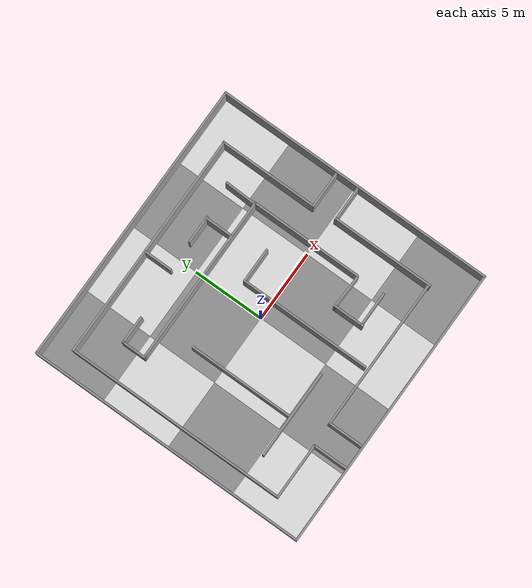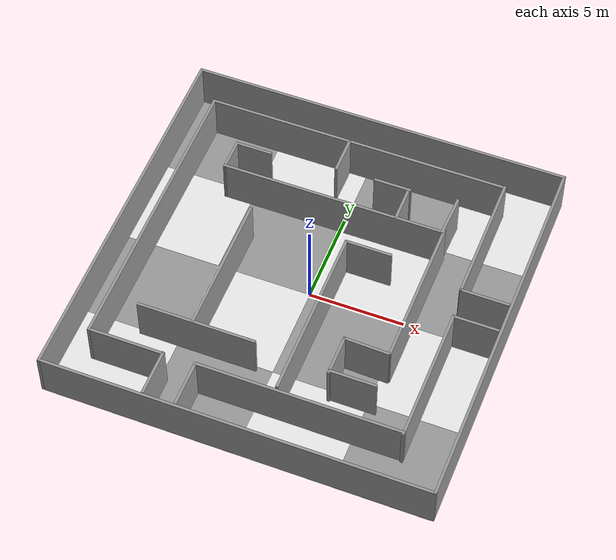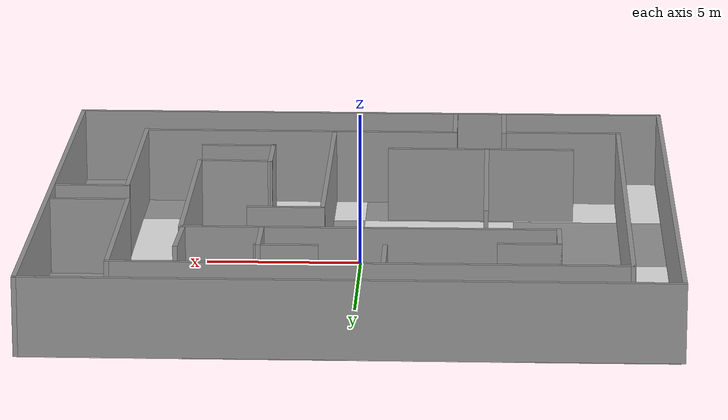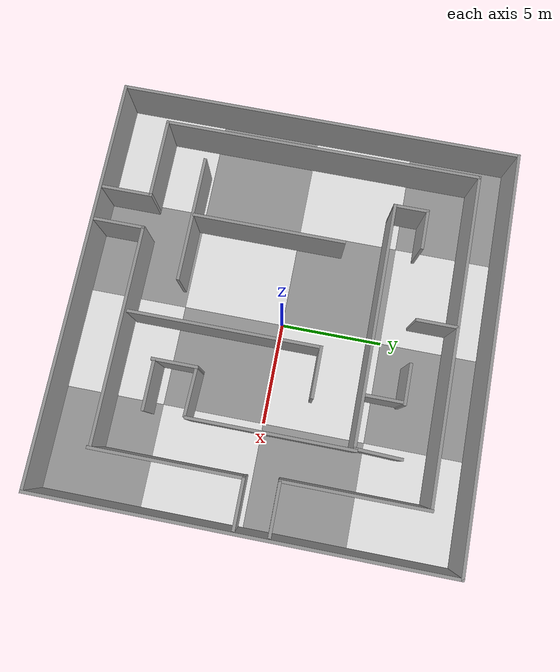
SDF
<?xml version="1.0" ?>
<sdf version="1.7">
  <world name="tb3_maze_academic_world">
    <physics name="default_physics" default="0" type="ode">
      <max_step_size>0.001</max_step_size>
      <real_time_factor>1.0</real_time_factor>
      <real_time_update_rate>1000</real_time_update_rate>
    </physics>

    <scene>
      <ambient>0.34 0.34 0.34 1</ambient>
      <background>0.96 0.96 0.96 1</background>
      <shadows>true</shadows>
    </scene>

    <light type="directional" name="soft_directional_light">
      <pose>0 0 15 0 0 0</pose>
      <cast_shadows>true</cast_shadows>
      <diffuse>0.82 0.82 0.82 1</diffuse>
      <specular>0.12 0.12 0.12 1</specular>
      <direction>-0.45 0.35 -1</direction>
    </light>

    <include>
      <uri>model://tb3_maze_world</uri>
    </include>

    <model name="checker_floor">
      <static>true</static>

      <link name="tile_00">
        <pose>-7.5 -7.5 -0.01 0 0 0</pose>
        <collision name="collision"><geometry><box><size>5 5 0.02</size></box></geometry></collision>
        <visual name="visual"><geometry><box><size>5 5 0.02</size></box></geometry><material><script><uri>file://media/materials/scripts/gazebo.material</uri><name>Gazebo/White</name></script></material></visual>
      </link>
      <link name="tile_01">
        <pose>-2.5 -7.5 -0.01 0 0 0</pose>
        <collision name="collision"><geometry><box><size>5 5 0.02</size></box></geometry></collision>
        <visual name="visual"><geometry><box><size>5 5 0.02</size></box></geometry><material><script><uri>file://media/materials/scripts/gazebo.material</uri><name>Gazebo/Grey</name></script></material></visual>
      </link>
      <link name="tile_02">
        <pose>2.5 -7.5 -0.01 0 0 0</pose>
        <collision name="collision"><geometry><box><size>5 5 0.02</size></box></geometry></collision>
        <visual name="visual"><geometry><box><size>5 5 0.02</size></box></geometry><material><script><uri>file://media/materials/scripts/gazebo.material</uri><name>Gazebo/White</name></script></material></visual>
      </link>
      <link name="tile_03">
        <pose>7.5 -7.5 -0.01 0 0 0</pose>
        <collision name="collision"><geometry><box><size>5 5 0.02</size></box></geometry></collision>
        <visual name="visual"><geometry><box><size>5 5 0.02</size></box></geometry><material><script><uri>file://media/materials/scripts/gazebo.material</uri><name>Gazebo/Grey</name></script></material></visual>
      </link>
      <link name="tile_10">
        <pose>-7.5 -2.5 -0.01 0 0 0</pose>
        <collision name="collision"><geometry><box><size>5 5 0.02</size></box></geometry></collision>
        <visual name="visual"><geometry><box><size>5 5 0.02</size></box></geometry><material><script><uri>file://media/materials/scripts/gazebo.material</uri><name>Gazebo/Grey</name></script></material></visual>
      </link>
      <link name="tile_11">
        <pose>-2.5 -2.5 -0.01 0 0 0</pose>
        <collision name="collision"><geometry><box><size>5 5 0.02</size></box></geometry></collision>
        <visual name="visual"><geometry><box><size>5 5 0.02</size></box></geometry><material><script><uri>file://media/materials/scripts/gazebo.material</uri><name>Gazebo/White</name></script></material></visual>
      </link>
      <link name="tile_12">
        <pose>2.5 -2.5 -0.01 0 0 0</pose>
        <collision name="collision"><geometry><box><size>5 5 0.02</size></box></geometry></collision>
        <visual name="visual"><geometry><box><size>5 5 0.02</size></box></geometry><material><script><uri>file://media/materials/scripts/gazebo.material</uri><name>Gazebo/Grey</name></script></material></visual>
      </link>
      <link name="tile_13">
        <pose>7.5 -2.5 -0.01 0 0 0</pose>
        <collision name="collision"><geometry><box><size>5 5 0.02</size></box></geometry></collision>
        <visual name="visual"><geometry><box><size>5 5 0.02</size></box></geometry><material><script><uri>file://media/materials/scripts/gazebo.material</uri><name>Gazebo/White</name></script></material></visual>
      </link>
      <link name="tile_20">
        <pose>-7.5 2.5 -0.01 0 0 0</pose>
        <collision name="collision"><geometry><box><size>5 5 0.02</size></box></geometry></collision>
        <visual name="visual"><geometry><box><size>5 5 0.02</size></box></geometry><material><script><uri>file://media/materials/scripts/gazebo.material</uri><name>Gazebo/White</name></script></material></visual>
      </link>
      <link name="tile_21">
        <pose>-2.5 2.5 -0.01 0 0 0</pose>
        <collision name="collision"><geometry><box><size>5 5 0.02</size></box></geometry></collision>
        <visual name="visual"><geometry><box><size>5 5 0.02</size></box></geometry><material><script><uri>file://media/materials/scripts/gazebo.material</uri><name>Gazebo/Grey</name></script></material></visual>
      </link>
      <link name="tile_22">
        <pose>2.5 2.5 -0.01 0 0 0</pose>
        <collision name="collision"><geometry><box><size>5 5 0.02</size></box></geometry></collision>
        <visual name="visual"><geometry><box><size>5 5 0.02</size></box></geometry><material><script><uri>file://media/materials/scripts/gazebo.material</uri><name>Gazebo/White</name></script></material></visual>
      </link>
      <link name="tile_23">
        <pose>7.5 2.5 -0.01 0 0 0</pose>
        <collision name="collision"><geometry><box><size>5 5 0.02</size></box></geometry></collision>
        <visual name="visual"><geometry><box><size>5 5 0.02</size></box></geometry><material><script><uri>file://media/materials/scripts/gazebo.material</uri><name>Gazebo/Grey</name></script></material></visual>
      </link>
      <link name="tile_30">
        <pose>-7.5 7.5 -0.01 0 0 0</pose>
        <collision name="collision"><geometry><box><size>5 5 0.02</size></box></geometry></collision>
        <visual name="visual"><geometry><box><size>5 5 0.02</size></box></geometry><material><script><uri>file://media/materials/scripts/gazebo.material</uri><name>Gazebo/Grey</name></script></material></visual>
      </link>
      <link name="tile_31">
        <pose>-2.5 7.5 -0.01 0 0 0</pose>
        <collision name="collision"><geometry><box><size>5 5 0.02</size></box></geometry></collision>
        <visual name="visual"><geometry><box><size>5 5 0.02</size></box></geometry><material><script><uri>file://media/materials/scripts/gazebo.material</uri><name>Gazebo/White</name></script></material></visual>
      </link>
      <link name="tile_32">
        <pose>2.5 7.5 -0.01 0 0 0</pose>
        <collision name="collision"><geometry><box><size>5 5 0.02</size></box></geometry></collision>
        <visual name="visual"><geometry><box><size>5 5 0.02</size></box></geometry><material><script><uri>file://media/materials/scripts/gazebo.material</uri><name>Gazebo/Grey</name></script></material></visual>
      </link>
      <link name="tile_33">
        <pose>7.5 7.5 -0.01 0 0 0</pose>
        <collision name="collision"><geometry><box><size>5 5 0.02</size></box></geometry></collision>
        <visual name="visual"><geometry><box><size>5 5 0.02</size></box></geometry><material><script><uri>file://media/materials/scripts/gazebo.material</uri><name>Gazebo/White</name></script></material></visual>
      </link>
    </model>
  </world>
</sdf>

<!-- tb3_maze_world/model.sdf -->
<sdf version='1.7'>
  <model name='tb3_maze_world'>
    <link name='Wall_0'>
      <pose>0 -9.925 0 0 -0 3.14159</pose>
      <self_collide>0</self_collide>
      <enable_wind>0</enable_wind>
      <kinematic>0</kinematic>
      <visual name='Wall_0_Visual'>
        <pose>0 0 1.25 0 -0 0</pose>
        <geometry>
          <box>
            <size>20.25 0.15 2.5</size>
          </box>
        </geometry>
        <material>
          <script>
            <uri>file://media/materials/scripts/gazebo.material</uri>
            <name>Gazebo/Grey</name>
          </script>
          <ambient>0.55 0.55 0.55 1</ambient>
          <shader type='pixel'/>
        </material>
        <meta>
          <layer>0</layer>
        </meta>
        <transparency>0</transparency>
        <cast_shadows>1</cast_shadows>
      </visual>
      <collision name='Wall_0_Collision'>
        <laser_retro>0</laser_retro>
        <max_contacts>10</max_contacts>
        <pose>0 0 1.25 0 -0 0</pose>
        <geometry>
          <box>
            <size>20.25 0.15 2.5</size>
          </box>
        </geometry>
        <surface>
          <friction>
            <ode>
              <mu>1</mu>
              <mu2>1</mu2>
              <fdir1>0 0 0</fdir1>
              <slip1>0</slip1>
              <slip2>0</slip2>
            </ode>
            <torsional>
              <coefficient>1</coefficient>
              <patch_radius>0</patch_radius>
              <surface_radius>0</surface_radius>
              <use_patch_radius>1</use_patch_radius>
              <ode>
                <slip>0</slip>
              </ode>
            </torsional>
          </friction>
          <bounce>
            <restitution_coefficient>0</restitution_coefficient>
            <threshold>1e+06</threshold>
          </bounce>
          <contact>
            <collide_without_contact>0</collide_without_contact>
            <collide_without_contact_bitmask>1</collide_without_contact_bitmask>
            <collide_bitmask>1</collide_bitmask>
            <ode>
              <soft_cfm>0</soft_cfm>
              <soft_erp>0.2</soft_erp>
              <kp>1e+13</kp>
              <kd>1</kd>
              <max_vel>0.01</max_vel>
              <min_depth>0</min_depth>
            </ode>
            <bullet>
              <split_impulse>1</split_impulse>
              <split_impulse_penetration_threshold>-0.01</split_impulse_penetration_threshold>
              <soft_cfm>0</soft_cfm>
              <soft_erp>0.2</soft_erp>
              <kp>1e+13</kp>
              <kd>1</kd>
            </bullet>
          </contact>
        </surface>
      </collision>
    </link>
    <link name='Wall_10'>
      <pose>-8.57134 0.376075 0 0 -0 1.5708</pose>
      <self_collide>0</self_collide>
      <enable_wind>0</enable_wind>
      <kinematic>0</kinematic>
      <visual name='Wall_10_Visual'>
        <pose>0 0 1.25 0 -0 0</pose>
        <geometry>
          <box>
            <size>15.75 0.15 2.5</size>
          </box>
        </geometry>
        <material>
          <script>
            <uri>file://media/materials/scripts/gazebo.material</uri>
            <name>Gazebo/Grey</name>
          </script>
          <ambient>0.55 0.55 0.55 1</ambient>
          <shader type='pixel'/>
        </material>
        <meta>
          <layer>0</layer>
        </meta>
        <transparency>0</transparency>
        <cast_shadows>1</cast_shadows>
      </visual>
      <collision name='Wall_10_Collision'>
        <laser_retro>0</laser_retro>
        <max_contacts>10</max_contacts>
        <pose>0 0 1.25 0 -0 0</pose>
        <geometry>
          <box>
            <size>15.75 0.15 2.5</size>
          </box>
        </geometry>
        <surface>
          <friction>
            <ode>
              <mu>1</mu>
              <mu2>1</mu2>
              <fdir1>0 0 0</fdir1>
              <slip1>0</slip1>
              <slip2>0</slip2>
            </ode>
            <torsional>
              <coefficient>1</coefficient>
              <patch_radius>0</patch_radius>
              <surface_radius>0</surface_radius>
              <use_patch_radius>1</use_patch_radius>
              <ode>
                <slip>0</slip>
              </ode>
            </torsional>
          </friction>
          <bounce>
            <restitution_coefficient>0</restitution_coefficient>
            <threshold>1e+06</threshold>
          </bounce>
          <contact>
            <collide_without_contact>0</collide_without_contact>
            <collide_without_contact_bitmask>1</collide_without_contact_bitmask>
            <collide_bitmask>1</collide_bitmask>
            <ode>
              <soft_cfm>0</soft_cfm>
              <soft_erp>0.2</soft_erp>
              <kp>1e+13</kp>
              <kd>1</kd>
              <max_vel>0.01</max_vel>
              <min_depth>0</min_depth>
            </ode>
            <bullet>
              <split_impulse>1</split_impulse>
              <split_impulse_penetration_threshold>-0.01</split_impulse_penetration_threshold>
              <soft_cfm>0</soft_cfm>
              <soft_erp>0.2</soft_erp>
              <kp>1e+13</kp>
              <kd>1</kd>
            </bullet>
          </contact>
        </surface>
      </collision>
    </link>
    <link name='Wall_11'>
      <pose>-0.579357 8.17574 0 0 0 -4.1e-05</pose>
      <self_collide>0</self_collide>
      <enable_wind>0</enable_wind>
      <kinematic>0</kinematic>
      <visual name='Wall_11_Visual'>
        <pose>0 0 1.25 0 -0 0</pose>
        <geometry>
          <box>
            <size>16.134 0.15 2.5</size>
          </box>
        </geometry>
        <material>
          <script>
            <uri>file://media/materials/scripts/gazebo.material</uri>
            <name>Gazebo/Grey</name>
          </script>
          <ambient>0.55 0.55 0.55 1</ambient>
          <shader type='pixel'/>
        </material>
        <meta>
          <layer>0</layer>
        </meta>
        <transparency>0</transparency>
        <cast_shadows>1</cast_shadows>
      </visual>
      <collision name='Wall_11_Collision'>
        <laser_retro>0</laser_retro>
        <max_contacts>10</max_contacts>
        <pose>0 0 1.25 0 -0 0</pose>
        <geometry>
          <box>
            <size>16.134 0.15 2.5</size>
          </box>
        </geometry>
        <surface>
          <friction>
            <ode>
              <mu>1</mu>
              <mu2>1</mu2>
              <fdir1>0 0 0</fdir1>
              <slip1>0</slip1>
              <slip2>0</slip2>
            </ode>
            <torsional>
              <coefficient>1</coefficient>
              <patch_radius>0</patch_radius>
              <surface_radius>0</surface_radius>
              <use_patch_radius>1</use_patch_radius>
              <ode>
                <slip>0</slip>
              </ode>
            </torsional>
          </friction>
          <bounce>
            <restitution_coefficient>0</restitution_coefficient>
            <threshold>1e+06</threshold>
          </bounce>
          <contact>
            <collide_without_contact>0</collide_without_contact>
            <collide_without_contact_bitmask>1</collide_without_contact_bitmask>
            <collide_bitmask>1</collide_bitmask>
            <ode>
              <soft_cfm>0</soft_cfm>
              <soft_erp>0.2</soft_erp>
              <kp>1e+13</kp>
              <kd>1</kd>
              <max_vel>0.01</max_vel>
              <min_depth>0</min_depth>
            </ode>
            <bullet>
              <split_impulse>1</split_impulse>
              <split_impulse_penetration_threshold>-0.01</split_impulse_penetration_threshold>
              <soft_cfm>0</soft_cfm>
              <soft_erp>0.2</soft_erp>
              <kp>1e+13</kp>
              <kd>1</kd>
            </bullet>
          </contact>
        </surface>
      </collision>
    </link>
    <link name='Wall_12'>
      <pose>7.4329 4.77069 0 0 0 -1.5708</pose>
      <self_collide>0</self_collide>
      <enable_wind>0</enable_wind>
      <kinematic>0</kinematic>
      <visual name='Wall_12_Visual'>
        <pose>0 0 1.25 0 -0 0</pose>
        <geometry>
          <box>
            <size>7 0.15 2.5</size>
          </box>
        </geometry>
        <material>
          <script>
            <uri>file://media/materials/scripts/gazebo.material</uri>
            <name>Gazebo/Grey</name>
          </script>
          <ambient>0.55 0.55 0.55 1</ambient>
          <shader type='pixel'/>
        </material>
        <meta>
          <layer>0</layer>
        </meta>
        <transparency>0</transparency>
        <cast_shadows>1</cast_shadows>
      </visual>
      <collision name='Wall_12_Collision'>
        <laser_retro>0</laser_retro>
        <max_contacts>10</max_contacts>
        <pose>0 0 1.25 0 -0 0</pose>
        <geometry>
          <box>
            <size>7 0.15 2.5</size>
          </box>
        </geometry>
        <surface>
          <friction>
            <ode>
              <mu>1</mu>
              <mu2>1</mu2>
              <fdir1>0 0 0</fdir1>
              <slip1>0</slip1>
              <slip2>0</slip2>
            </ode>
            <torsional>
              <coefficient>1</coefficient>
              <patch_radius>0</patch_radius>
              <surface_radius>0</surface_radius>
              <use_patch_radius>1</use_patch_radius>
              <ode>
                <slip>0</slip>
              </ode>
            </torsional>
          </friction>
          <bounce>
            <restitution_coefficient>0</restitution_coefficient>
            <threshold>1e+06</threshold>
          </bounce>
          <contact>
            <collide_without_contact>0</collide_without_contact>
            <collide_without_contact_bitmask>1</collide_without_contact_bitmask>
            <collide_bitmask>1</collide_bitmask>
            <ode>
              <soft_cfm>0</soft_cfm>
              <soft_erp>0.2</soft_erp>
              <kp>1e+13</kp>
              <kd>1</kd>
              <max_vel>0.01</max_vel>
              <min_depth>0</min_depth>
            </ode>
            <bullet>
              <split_impulse>1</split_impulse>
              <split_impulse_penetration_threshold>-0.01</split_impulse_penetration_threshold>
              <soft_cfm>0</soft_cfm>
              <soft_erp>0.2</soft_erp>
              <kp>1e+13</kp>
              <kd>1</kd>
            </bullet>
          </contact>
        </surface>
      </collision>
    </link>
    <link name='Wall_13'>
      <pose>8.66564 1.32574 0 0 -0 0.000335</pose>
      <self_collide>0</self_collide>
      <enable_wind>0</enable_wind>
      <kinematic>0</kinematic>
      <gravity>1</gravity>
      <inertial>
        <mass>1</mass>
        <pose>0 0 0 0 -0 0</pose>
        <inertia>
          <ixx>1</ixx>
          <ixy>0</ixy>
          <ixz>0</ixz>
          <iyy>1</iyy>
          <iyz>0</iyz>
          <izz>1</izz>
        </inertia>
      </inertial>
      <visual name='Wall_13_Visual'>
        <pose>0 0 1.25 0 -0 0</pose>
        <geometry>
          <box>
            <size>2.55604 0.15 2.5</size>
          </box>
        </geometry>
        <material>
          <script>
            <uri>file://media/materials/scripts/gazebo.material</uri>
            <name>Gazebo/Grey</name>
          </script>
          <ambient>0.55 0.55 0.55 1</ambient>
          <shader type='pixel'>
            <normal_map>__default__</normal_map>
          </shader>
          <diffuse>1 1 1 1</diffuse>
          <specular>0.05 0.05 0.05 1</specular>
          <emissive>0 0 0 1</emissive>
        </material>
        <meta>
          <layer>0</layer>
        </meta>
        <transparency>0</transparency>
        <cast_shadows>1</cast_shadows>
      </visual>
      <collision name='Wall_13_Collision'>
        <laser_retro>0</laser_retro>
        <max_contacts>10</max_contacts>
        <pose>0 0 1.25 0 -0 0</pose>
        <geometry>
          <box>
            <size>2.55604 0.15 2.5</size>
          </box>
        </geometry>
        <surface>
          <friction>
            <ode>
              <mu>1</mu>
              <mu2>1</mu2>
              <fdir1>0 0 0</fdir1>
              <slip1>0</slip1>
              <slip2>0</slip2>
            </ode>
            <torsional>
              <coefficient>1</coefficient>
              <patch_radius>0</patch_radius>
              <surface_radius>0</surface_radius>
              <use_patch_radius>1</use_patch_radius>
              <ode>
                <slip>0</slip>
              </ode>
            </torsional>
          </friction>
          <bounce>
            <restitution_coefficient>0</restitution_coefficient>
            <threshold>1e+06</threshold>
          </bounce>
          <contact>
            <collide_without_contact>0</collide_without_contact>
            <collide_without_contact_bitmask>1</collide_without_contact_bitmask>
            <collide_bitmask>1</collide_bitmask>
            <ode>
              <soft_cfm>0</soft_cfm>
              <soft_erp>0.2</soft_erp>
              <kp>1e+13</kp>
              <kd>1</kd>
              <max_vel>0.01</max_vel>
              <min_depth>0</min_depth>
            </ode>
            <bullet>
              <split_impulse>1</split_impulse>
              <split_impulse_penetration_threshold>-0.01</split_impulse_penetration_threshold>
              <soft_cfm>0</soft_cfm>
              <soft_erp>0.2</soft_erp>
              <kp>1e+13</kp>
              <kd>1</kd>
            </bullet>
          </contact>
        </surface>
      </collision>
    </link>
    <link name='Wall_15'>
      <pose>8.73819 -0.299308 0 0 -0 3.14159</pose>
      <self_collide>0</self_collide>
      <enable_wind>0</enable_wind>
      <kinematic>0</kinematic>
      <gravity>1</gravity>
      <inertial>
        <mass>1</mass>
        <pose>0 0 0 0 -0 0</pose>
        <inertia>
          <ixx>1</ixx>
          <ixy>0</ixy>
          <ixz>0</ixz>
          <iyy>1</iyy>
          <iyz>0</iyz>
          <izz>1</izz>
        </inertia>
      </inertial>
      <visual name='Wall_15_Visual'>
        <pose>0 0 1.25 0 -0 0</pose>
        <geometry>
          <box>
            <size>2.43 0.15 2.5</size>
          </box>
        </geometry>
        <material>
          <script>
            <uri>file://media/materials/scripts/gazebo.material</uri>
            <name>Gazebo/Grey</name>
          </script>
          <ambient>0.55 0.55 0.55 1</ambient>
          <shader type='pixel'>
            <normal_map>__default__</normal_map>
          </shader>
          <diffuse>1 1 1 1</diffuse>
          <specular>0.05 0.05 0.05 1</specular>
          <emissive>0 0 0 1</emissive>
        </material>
        <meta>
          <layer>0</layer>
        </meta>
        <transparency>0</transparency>
        <cast_shadows>1</cast_shadows>
      </visual>
      <collision name='Wall_15_Collision'>
        <laser_retro>0</laser_retro>
        <max_contacts>10</max_contacts>
        <pose>0 0 1.25 0 -0 0</pose>
        <geometry>
          <box>
            <size>2.43 0.15 2.5</size>
          </box>
        </geometry>
        <surface>
          <friction>
            <ode>
              <mu>1</mu>
              <mu2>1</mu2>
              <fdir1>0 0 0</fdir1>
              <slip1>0</slip1>
              <slip2>0</slip2>
            </ode>
            <torsional>
              <coefficient>1</coefficient>
              <patch_radius>0</patch_radius>
              <surface_radius>0</surface_radius>
              <use_patch_radius>1</use_patch_radius>
              <ode>
                <slip>0</slip>
              </ode>
            </torsional>
          </friction>
          <bounce>
            <restitution_coefficient>0</restitution_coefficient>
            <threshold>1e+06</threshold>
          </bounce>
          <contact>
            <collide_without_contact>0</collide_without_contact>
            <collide_without_contact_bitmask>1</collide_without_contact_bitmask>
            <collide_bitmask>1</collide_bitmask>
            <ode>
              <soft_cfm>0</soft_cfm>
              <soft_erp>0.2</soft_erp>
              <kp>1e+13</kp>
              <kd>1</kd>
              <max_vel>0.01</max_vel>
              <min_depth>0</min_depth>
            </ode>
            <bullet>
              <split_impulse>1</split_impulse>
              <split_impulse_penetration_threshold>-0.01</split_impulse_penetration_threshold>
              <soft_cfm>0</soft_cfm>
              <soft_erp>0.2</soft_erp>
              <kp>1e+13</kp>
              <kd>1</kd>
            </bullet>
          </contact>
        </surface>
      </collision>
    </link>
    <link name='Wall_16'>
      <pose>7.60819 -3.88746 0 0 0 -1.5708</pose>
      <self_collide>0</self_collide>
      <enable_wind>0</enable_wind>
      <kinematic>0</kinematic>
      <visual name='Wall_16_Visual'>
        <pose>0 0 1.25 0 -0 0</pose>
        <geometry>
          <box>
            <size>7.3263 0.15 2.5</size>
          </box>
        </geometry>
        <material>
          <script>
            <uri>file://media/materials/scripts/gazebo.material</uri>
            <name>Gazebo/Grey</name>
          </script>
          <ambient>0.55 0.55 0.55 1</ambient>
          <shader type='pixel'/>
        </material>
        <meta>
          <layer>0</layer>
        </meta>
        <transparency>0</transparency>
        <cast_shadows>1</cast_shadows>
      </visual>
      <collision name='Wall_16_Collision'>
        <laser_retro>0</laser_retro>
        <max_contacts>10</max_contacts>
        <pose>0 0 1.25 0 -0 0</pose>
        <geometry>
          <box>
            <size>7.3263 0.15 2.5</size>
          </box>
        </geometry>
        <surface>
          <friction>
            <ode>
              <mu>1</mu>
              <mu2>1</mu2>
              <fdir1>0 0 0</fdir1>
              <slip1>0</slip1>
              <slip2>0</slip2>
            </ode>
            <torsional>
              <coefficient>1</coefficient>
              <patch_radius>0</patch_radius>
              <surface_radius>0</surface_radius>
              <use_patch_radius>1</use_patch_radius>
              <ode>
                <slip>0</slip>
              </ode>
            </torsional>
          </friction>
          <bounce>
            <restitution_coefficient>0</restitution_coefficient>
            <threshold>1e+06</threshold>
          </bounce>
          <contact>
            <collide_without_contact>0</collide_without_contact>
            <collide_without_contact_bitmask>1</collide_without_contact_bitmask>
            <collide_bitmask>1</collide_bitmask>
            <ode>
              <soft_cfm>0</soft_cfm>
              <soft_erp>0.2</soft_erp>
              <kp>1e+13</kp>
              <kd>1</kd>
              <max_vel>0.01</max_vel>
              <min_depth>0</min_depth>
            </ode>
            <bullet>
              <split_impulse>1</split_impulse>
              <split_impulse_penetration_threshold>-0.01</split_impulse_penetration_threshold>
              <soft_cfm>0</soft_cfm>
              <soft_erp>0.2</soft_erp>
              <kp>1e+13</kp>
              <kd>1</kd>
            </bullet>
          </contact>
        </surface>
      </collision>
    </link>
    <link name='Wall_17'>
      <pose>2.30819 -7.39403 0 0 -0 3.14159</pose>
      <self_collide>0</self_collide>
      <enable_wind>0</enable_wind>
      <kinematic>0</kinematic>
      <visual name='Wall_17_Visual'>
        <pose>0 0 1.25 0 -0 0</pose>
        <geometry>
          <box>
            <size>10.75 0.15 2.5</size>
          </box>
        </geometry>
        <material>
          <script>
            <uri>file://media/materials/scripts/gazebo.material</uri>
            <name>Gazebo/Grey</name>
          </script>
          <ambient>0.55 0.55 0.55 1</ambient>
          <shader type='pixel'/>
        </material>
        <meta>
          <layer>0</layer>
        </meta>
        <transparency>0</transparency>
        <cast_shadows>1</cast_shadows>
      </visual>
      <collision name='Wall_17_Collision'>
        <laser_retro>0</laser_retro>
        <max_contacts>10</max_contacts>
        <pose>0 0 1.25 0 -0 0</pose>
        <geometry>
          <box>
            <size>10.75 0.15 2.5</size>
          </box>
        </geometry>
        <surface>
          <friction>
            <ode>
              <mu>1</mu>
              <mu2>1</mu2>
              <fdir1>0 0 0</fdir1>
              <slip1>0</slip1>
              <slip2>0</slip2>
            </ode>
            <torsional>
              <coefficient>1</coefficient>
              <patch_radius>0</patch_radius>
              <surface_radius>0</surface_radius>
              <use_patch_radius>1</use_patch_radius>
              <ode>
                <slip>0</slip>
              </ode>
            </torsional>
          </friction>
          <bounce>
            <restitution_coefficient>0</restitution_coefficient>
            <threshold>1e+06</threshold>
          </bounce>
          <contact>
            <collide_without_contact>0</collide_without_contact>
            <collide_without_contact_bitmask>1</collide_without_contact_bitmask>
            <collide_bitmask>1</collide_bitmask>
            <ode>
              <soft_cfm>0</soft_cfm>
              <soft_erp>0.2</soft_erp>
              <kp>1e+13</kp>
              <kd>1</kd>
              <max_vel>0.01</max_vel>
              <min_depth>0</min_depth>
            </ode>
            <bullet>
              <split_impulse>1</split_impulse>
              <split_impulse_penetration_threshold>-0.01</split_impulse_penetration_threshold>
              <soft_cfm>0</soft_cfm>
              <soft_erp>0.2</soft_erp>
              <kp>1e+13</kp>
              <kd>1</kd>
            </bullet>
          </contact>
        </surface>
      </collision>
    </link>
    <link name='Wall_18'>
      <pose>-2.99181 -8.59 0 0 0 -1.5708</pose>
      <self_collide>0</self_collide>
      <enable_wind>0</enable_wind>
      <kinematic>0</kinematic>
      <gravity>1</gravity>
      <inertial>
        <mass>1</mass>
        <pose>0 0 0 0 -0 0</pose>
        <inertia>
          <ixx>1</ixx>
          <ixy>0</ixy>
          <ixz>0</ixz>
          <iyy>1</iyy>
          <iyz>0</iyz>
          <izz>1</izz>
        </inertia>
      </inertial>
      <visual name='Wall_18_Visual'>
        <pose>0 0 1.25 0 -0 0</pose>
        <geometry>
          <box>
            <size>2.5 0.15 2.5</size>
          </box>
        </geometry>
        <material>
          <script>
            <uri>file://media/materials/scripts/gazebo.material</uri>
            <name>Gazebo/Grey</name>
          </script>
          <ambient>0.55 0.55 0.55 1</ambient>
          <shader type='pixel'>
            <normal_map>__default__</normal_map>
          </shader>
          <diffuse>1 1 1 1</diffuse>
          <specular>0.05 0.05 0.05 1</specular>
          <emissive>0 0 0 1</emissive>
        </material>
        <meta>
          <layer>0</layer>
        </meta>
        <transparency>0</transparency>
        <cast_shadows>1</cast_shadows>
      </visual>
      <collision name='Wall_18_Collision'>
        <laser_retro>0</laser_retro>
        <max_contacts>10</max_contacts>
        <pose>0 0 1.25 0 -0 0</pose>
        <geometry>
          <box>
            <size>2.5 0.15 2.5</size>
          </box>
        </geometry>
        <surface>
          <friction>
            <ode>
              <mu>1</mu>
              <mu2>1</mu2>
              <fdir1>0 0 0</fdir1>
              <slip1>0</slip1>
              <slip2>0</slip2>
            </ode>
            <torsional>
              <coefficient>1</coefficient>
              <patch_radius>0</patch_radius>
              <surface_radius>0</surface_radius>
              <use_patch_radius>1</use_patch_radius>
              <ode>
                <slip>0</slip>
              </ode>
            </torsional>
          </friction>
          <bounce>
            <restitution_coefficient>0</restitution_coefficient>
            <threshold>1e+06</threshold>
          </bounce>
          <contact>
            <collide_without_contact>0</collide_without_contact>
            <collide_without_contact_bitmask>1</collide_without_contact_bitmask>
            <collide_bitmask>1</collide_bitmask>
            <ode>
              <soft_cfm>0</soft_cfm>
              <soft_erp>0.2</soft_erp>
              <kp>1e+13</kp>
              <kd>1</kd>
              <max_vel>0.01</max_vel>
              <min_depth>0</min_depth>
            </ode>
            <bullet>
              <split_impulse>1</split_impulse>
              <split_impulse_penetration_threshold>-0.01</split_impulse_penetration_threshold>
              <soft_cfm>0</soft_cfm>
              <soft_erp>0.2</soft_erp>
              <kp>1e+13</kp>
              <kd>1</kd>
            </bullet>
          </contact>
        </surface>
      </collision>
    </link>
    <link name='Wall_2'>
      <pose>-10.05 0 0 0 -0 1.5708</pose>
      <self_collide>0</self_collide>
      <enable_wind>0</enable_wind>
      <kinematic>0</kinematic>
      <visual name='Wall_2_Visual'>
        <pose>0 0 1.25 0 -0 0</pose>
        <geometry>
          <box>
            <size>20 0.15 2.5</size>
          </box>
        </geometry>
        <material>
          <script>
            <uri>file://media/materials/scripts/gazebo.material</uri>
            <name>Gazebo/Grey</name>
          </script>
          <ambient>0.55 0.55 0.55 1</ambient>
          <shader type='pixel'/>
        </material>
        <meta>
          <layer>0</layer>
        </meta>
        <transparency>0</transparency>
        <cast_shadows>1</cast_shadows>
      </visual>
      <collision name='Wall_2_Collision'>
        <laser_retro>0</laser_retro>
        <max_contacts>10</max_contacts>
        <pose>0 0 1.25 0 -0 0</pose>
        <geometry>
          <box>
            <size>20 0.15 2.5</size>
          </box>
        </geometry>
        <surface>
          <friction>
            <ode>
              <mu>1</mu>
              <mu2>1</mu2>
              <fdir1>0 0 0</fdir1>
              <slip1>0</slip1>
              <slip2>0</slip2>
            </ode>
            <torsional>
              <coefficient>1</coefficient>
              <patch_radius>0</patch_radius>
              <surface_radius>0</surface_radius>
              <use_patch_radius>1</use_patch_radius>
              <ode>
                <slip>0</slip>
              </ode>
            </torsional>
          </friction>
          <bounce>
            <restitution_coefficient>0</restitution_coefficient>
            <threshold>1e+06</threshold>
          </bounce>
          <contact>
            <collide_without_contact>0</collide_without_contact>
            <collide_without_contact_bitmask>1</collide_without_contact_bitmask>
            <collide_bitmask>1</collide_bitmask>
            <ode>
              <soft_cfm>0</soft_cfm>
              <soft_erp>0.2</soft_erp>
              <kp>1e+13</kp>
              <kd>1</kd>
              <max_vel>0.01</max_vel>
              <min_depth>0</min_depth>
            </ode>
            <bullet>
              <split_impulse>1</split_impulse>
              <split_impulse_penetration_threshold>-0.01</split_impulse_penetration_threshold>
              <soft_cfm>0</soft_cfm>
              <soft_erp>0.2</soft_erp>
              <kp>1e+13</kp>
              <kd>1</kd>
            </bullet>
          </contact>
        </surface>
      </collision>
    </link>
    <link name='Wall_20'>
      <pose>-3.89345 -5.19374 0 0 -0 0</pose>
      <self_collide>0</self_collide>
      <enable_wind>0</enable_wind>
      <kinematic>0</kinematic>
      <visual name='Wall_20_Visual'>
        <pose>0 0 1.25 0 -0 0</pose>
        <geometry>
          <box>
            <size>6.25 0.15 2.5</size>
          </box>
        </geometry>
        <material>
          <script>
            <uri>file://media/materials/scripts/gazebo.material</uri>
            <name>Gazebo/Grey</name>
          </script>
          <ambient>0.55 0.55 0.55 1</ambient>
          <shader type='pixel'/>
        </material>
        <meta>
          <layer>0</layer>
        </meta>
        <transparency>0</transparency>
        <cast_shadows>1</cast_shadows>
      </visual>
      <collision name='Wall_20_Collision'>
        <laser_retro>0</laser_retro>
        <max_contacts>10</max_contacts>
        <pose>0 0 1.25 0 -0 0</pose>
        <geometry>
          <box>
            <size>6.25 0.15 2.5</size>
          </box>
        </geometry>
        <surface>
          <friction>
            <ode>
              <mu>1</mu>
              <mu2>1</mu2>
              <fdir1>0 0 0</fdir1>
              <slip1>0</slip1>
              <slip2>0</slip2>
            </ode>
            <torsional>
              <coefficient>1</coefficient>
              <patch_radius>0</patch_radius>
              <surface_radius>0</surface_radius>
              <use_patch_radius>1</use_patch_radius>
              <ode>
                <slip>0</slip>
              </ode>
            </torsional>
          </friction>
          <bounce>
            <restitution_coefficient>0</restitution_coefficient>
            <threshold>1e+06</threshold>
          </bounce>
          <contact>
            <collide_without_contact>0</collide_without_contact>
            <collide_without_contact_bitmask>1</collide_without_contact_bitmask>
            <collide_bitmask>1</collide_bitmask>
            <ode>
              <soft_cfm>0</soft_cfm>
              <soft_erp>0.2</soft_erp>
              <kp>1e+13</kp>
              <kd>1</kd>
              <max_vel>0.01</max_vel>
              <min_depth>0</min_depth>
            </ode>
            <bullet>
              <split_impulse>1</split_impulse>
              <split_impulse_penetration_threshold>-0.01</split_impulse_penetration_threshold>
              <soft_cfm>0</soft_cfm>
              <soft_erp>0.2</soft_erp>
              <kp>1e+13</kp>
              <kd>1</kd>
            </bullet>
          </contact>
        </surface>
      </collision>
    </link>
    <link name='Wall_23'>
      <pose>-4.08836 -1.43717 0 0 -0 1.5708</pose>
      <self_collide>0</self_collide>
      <enable_wind>0</enable_wind>
      <kinematic>0</kinematic>
      <visual name='Wall_23_Visual'>
        <pose>0 0 1.25 0 -0 0</pose>
        <geometry>
          <box>
            <size>7.5 0.15 2.5</size>
          </box>
        </geometry>
        <material>
          <script>
            <uri>file://media/materials/scripts/gazebo.material</uri>
            <name>Gazebo/Grey</name>
          </script>
          <ambient>0.55 0.55 0.55 1</ambient>
          <shader type='pixel'/>
        </material>
        <meta>
          <layer>0</layer>
        </meta>
        <transparency>0</transparency>
        <cast_shadows>1</cast_shadows>
      </visual>
      <collision name='Wall_23_Collision'>
        <laser_retro>0</laser_retro>
        <max_contacts>10</max_contacts>
        <pose>0 0 1.25 0 -0 0</pose>
        <geometry>
          <box>
            <size>7.5 0.15 2.5</size>
          </box>
        </geometry>
        <surface>
          <friction>
            <ode>
              <mu>1</mu>
              <mu2>1</mu2>
              <fdir1>0 0 0</fdir1>
              <slip1>0</slip1>
              <slip2>0</slip2>
            </ode>
            <torsional>
              <coefficient>1</coefficient>
              <patch_radius>0</patch_radius>
              <surface_radius>0</surface_radius>
              <use_patch_radius>1</use_patch_radius>
              <ode>
                <slip>0</slip>
              </ode>
            </torsional>
          </friction>
          <bounce>
            <restitution_coefficient>0</restitution_coefficient>
            <threshold>1e+06</threshold>
          </bounce>
          <contact>
            <collide_without_contact>0</collide_without_contact>
            <collide_without_contact_bitmask>1</collide_without_contact_bitmask>
            <collide_bitmask>1</collide_bitmask>
            <ode>
              <soft_cfm>0</soft_cfm>
              <soft_erp>0.2</soft_erp>
              <kp>1e+13</kp>
              <kd>1</kd>
              <max_vel>0.01</max_vel>
              <min_depth>0</min_depth>
            </ode>
            <bullet>
              <split_impulse>1</split_impulse>
              <split_impulse_penetration_threshold>-0.01</split_impulse_penetration_threshold>
              <soft_cfm>0</soft_cfm>
              <soft_erp>0.2</soft_erp>
              <kp>1e+13</kp>
              <kd>1</kd>
            </bullet>
          </contact>
        </surface>
      </collision>
    </link>
    <link name='Wall_25'>
      <pose>1.13237 -2.58107 0 0 0 -1.5708</pose>
      <self_collide>0</self_collide>
      <enable_wind>0</enable_wind>
      <kinematic>0</kinematic>
      <visual name='Wall_25_Visual'>
        <pose>0 0 1.25 0 -0 0</pose>
        <geometry>
          <box>
            <size>9.28167 0.15 2.5</size>
          </box>
        </geometry>
        <material>
          <script>
            <uri>file://media/materials/scripts/gazebo.material</uri>
            <name>Gazebo/Grey</name>
          </script>
          <ambient>0.55 0.55 0.55 1</ambient>
          <shader type='pixel'/>
        </material>
        <meta>
          <layer>0</layer>
        </meta>
        <transparency>0</transparency>
        <cast_shadows>1</cast_shadows>
      </visual>
      <collision name='Wall_25_Collision'>
        <laser_retro>0</laser_retro>
        <max_contacts>10</max_contacts>
        <pose>0 0 1.25 0 -0 0</pose>
        <geometry>
          <box>
            <size>9.28167 0.15 2.5</size>
          </box>
        </geometry>
        <surface>
          <friction>
            <ode>
              <mu>1</mu>
              <mu2>1</mu2>
              <fdir1>0 0 0</fdir1>
              <slip1>0</slip1>
              <slip2>0</slip2>
            </ode>
            <torsional>
              <coefficient>1</coefficient>
              <patch_radius>0</patch_radius>
              <surface_radius>0</surface_radius>
              <use_patch_radius>1</use_patch_radius>
              <ode>
                <slip>0</slip>
              </ode>
            </torsional>
          </friction>
          <bounce>
            <restitution_coefficient>0</restitution_coefficient>
            <threshold>1e+06</threshold>
          </bounce>
          <contact>
            <collide_without_contact>0</collide_without_contact>
            <collide_without_contact_bitmask>1</collide_without_contact_bitmask>
            <collide_bitmask>1</collide_bitmask>
            <ode>
              <soft_cfm>0</soft_cfm>
              <soft_erp>0.2</soft_erp>
              <kp>1e+13</kp>
              <kd>1</kd>
              <max_vel>0.01</max_vel>
              <min_depth>0</min_depth>
            </ode>
            <bullet>
              <split_impulse>1</split_impulse>
              <split_impulse_penetration_threshold>-0.01</split_impulse_penetration_threshold>
              <soft_cfm>0</soft_cfm>
              <soft_erp>0.2</soft_erp>
              <kp>1e+13</kp>
              <kd>1</kd>
            </bullet>
          </contact>
        </surface>
      </collision>
    </link>
    <link name='Wall_27'>
      <pose>2.30737 2.06634 0 0 -0 0</pose>
      <self_collide>0</self_collide>
      <enable_wind>0</enable_wind>
      <kinematic>0</kinematic>
      <visual name='Wall_27_Visual'>
        <pose>0 0 1.25 0 -0 0</pose>
        <geometry>
          <box>
            <size>2.5 0.15 2.5</size>
          </box>
        </geometry>
        <material>
          <script>
            <uri>file://media/materials/scripts/gazebo.material</uri>
            <name>Gazebo/Grey</name>
          </script>
          <ambient>0.55 0.55 0.55 1</ambient>
          <shader type='pixel'/>
        </material>
        <meta>
          <layer>0</layer>
        </meta>
        <transparency>0</transparency>
        <cast_shadows>1</cast_shadows>
      </visual>
      <collision name='Wall_27_Collision'>
        <laser_retro>0</laser_retro>
        <max_contacts>10</max_contacts>
        <pose>0 0 1.25 0 -0 0</pose>
        <geometry>
          <box>
            <size>2.5 0.15 2.5</size>
          </box>
        </geometry>
        <surface>
          <friction>
            <ode>
              <mu>1</mu>
              <mu2>1</mu2>
              <fdir1>0 0 0</fdir1>
              <slip1>0</slip1>
              <slip2>0</slip2>
            </ode>
            <torsional>
              <coefficient>1</coefficient>
              <patch_radius>0</patch_radius>
              <surface_radius>0</surface_radius>
              <use_patch_radius>1</use_patch_radius>
              <ode>
                <slip>0</slip>
              </ode>
            </torsional>
          </friction>
          <bounce>
            <restitution_coefficient>0</restitution_coefficient>
            <threshold>1e+06</threshold>
          </bounce>
          <contact>
            <collide_without_contact>0</collide_without_contact>
            <collide_without_contact_bitmask>1</collide_without_contact_bitmask>
            <collide_bitmask>1</collide_bitmask>
            <ode>
              <soft_cfm>0</soft_cfm>
              <soft_erp>0.2</soft_erp>
              <kp>1e+13</kp>
              <kd>1</kd>
              <max_vel>0.01</max_vel>
              <min_depth>0</min_depth>
            </ode>
            <bullet>
              <split_impulse>1</split_impulse>
              <split_impulse_penetration_threshold>-0.01</split_impulse_penetration_threshold>
              <soft_cfm>0</soft_cfm>
              <soft_erp>0.2</soft_erp>
              <kp>1e+13</kp>
              <kd>1</kd>
            </bullet>
          </contact>
        </surface>
      </collision>
    </link>
    <link name='Wall_29'>
      <pose>-0.482899 4.35573 0 0 -0 0.000903</pose>
      <self_collide>0</self_collide>
      <enable_wind>0</enable_wind>
      <kinematic>0</kinematic>
      <visual name='Wall_29_Visual'>
        <pose>0 0 1.25 0 -0 0</pose>
        <geometry>
          <box>
            <size>11.9291 0.15 2.5</size>
          </box>
        </geometry>
        <material>
          <script>
            <uri>file://media/materials/scripts/gazebo.material</uri>
            <name>Gazebo/Grey</name>
          </script>
          <ambient>0.55 0.55 0.55 1</ambient>
          <shader type='pixel'/>
        </material>
        <meta>
          <layer>0</layer>
        </meta>
        <transparency>0</transparency>
        <cast_shadows>1</cast_shadows>
      </visual>
      <collision name='Wall_29_Collision'>
        <laser_retro>0</laser_retro>
        <max_contacts>10</max_contacts>
        <pose>0 0 1.25 0 -0 0</pose>
        <geometry>
          <box>
            <size>11.9291 0.15 2.5</size>
          </box>
        </geometry>
        <surface>
          <friction>
            <ode>
              <mu>1</mu>
              <mu2>1</mu2>
              <fdir1>0 0 0</fdir1>
              <slip1>0</slip1>
              <slip2>0</slip2>
            </ode>
            <torsional>
              <coefficient>1</coefficient>
              <patch_radius>0</patch_radius>
              <surface_radius>0</surface_radius>
              <use_patch_radius>1</use_patch_radius>
              <ode>
                <slip>0</slip>
              </ode>
            </torsional>
          </friction>
          <bounce>
            <restitution_coefficient>0</restitution_coefficient>
            <threshold>1e+06</threshold>
          </bounce>
          <contact>
            <collide_without_contact>0</collide_without_contact>
            <collide_without_contact_bitmask>1</collide_without_contact_bitmask>
            <collide_bitmask>1</collide_bitmask>
            <ode>
              <soft_cfm>0</soft_cfm>
              <soft_erp>0.2</soft_erp>
              <kp>1e+13</kp>
              <kd>1</kd>
              <max_vel>0.01</max_vel>
              <min_depth>0</min_depth>
            </ode>
            <bullet>
              <split_impulse>1</split_impulse>
              <split_impulse_penetration_threshold>-0.01</split_impulse_penetration_threshold>
              <soft_cfm>0</soft_cfm>
              <soft_erp>0.2</soft_erp>
              <kp>1e+13</kp>
              <kd>1</kd>
            </bullet>
          </contact>
        </surface>
      </collision>
    </link>
    <link name='Wall_30'>
      <pose>5.47757 0.501702 0 0 0 -1.5708</pose>
      <self_collide>0</self_collide>
      <enable_wind>0</enable_wind>
      <kinematic>0</kinematic>
      <visual name='Wall_30_Visual'>
        <pose>0 0 1.25 0 -0 0</pose>
        <geometry>
          <box>
            <size>8.01056 0.15 2.5</size>
          </box>
        </geometry>
        <material>
          <script>
            <uri>file://media/materials/scripts/gazebo.material</uri>
            <name>Gazebo/Grey</name>
          </script>
          <ambient>0.55 0.55 0.55 1</ambient>
          <shader type='pixel'/>
        </material>
        <meta>
          <layer>0</layer>
        </meta>
        <transparency>0</transparency>
        <cast_shadows>1</cast_shadows>
      </visual>
      <collision name='Wall_30_Collision'>
        <laser_retro>0</laser_retro>
        <max_contacts>10</max_contacts>
        <pose>0 0 1.25 0 -0 0</pose>
        <geometry>
          <box>
            <size>8.01056 0.15 2.5</size>
          </box>
        </geometry>
        <surface>
          <friction>
            <ode>
              <mu>1</mu>
              <mu2>1</mu2>
              <fdir1>0 0 0</fdir1>
              <slip1>0</slip1>
              <slip2>0</slip2>
            </ode>
            <torsional>
              <coefficient>1</coefficient>
              <patch_radius>0</patch_radius>
              <surface_radius>0</surface_radius>
              <use_patch_radius>1</use_patch_radius>
              <ode>
                <slip>0</slip>
              </ode>
            </torsional>
          </friction>
          <bounce>
            <restitution_coefficient>0</restitution_coefficient>
            <threshold>1e+06</threshold>
          </bounce>
          <contact>
            <collide_without_contact>0</collide_without_contact>
            <collide_without_contact_bitmask>1</collide_without_contact_bitmask>
            <collide_bitmask>1</collide_bitmask>
            <ode>
              <soft_cfm>0</soft_cfm>
              <soft_erp>0.2</soft_erp>
              <kp>1e+13</kp>
              <kd>1</kd>
              <max_vel>0.01</max_vel>
              <min_depth>0</min_depth>
            </ode>
            <bullet>
              <split_impulse>1</split_impulse>
              <split_impulse_penetration_threshold>-0.01</split_impulse_penetration_threshold>
              <soft_cfm>0</soft_cfm>
              <soft_erp>0.2</soft_erp>
              <kp>1e+13</kp>
              <kd>1</kd>
            </bullet>
          </contact>
        </surface>
      </collision>
    </link>
    <link name='Wall_31'>
      <pose>4.2671 -3.46404 0 0 -0 3.11048</pose>
      <self_collide>0</self_collide>
      <enable_wind>0</enable_wind>
      <kinematic>0</kinematic>
      <visual name='Wall_31_Visual'>
        <pose>0 0 1.25 0 -0 0</pose>
        <geometry>
          <box>
            <size>2.43017 0.15 2.5</size>
          </box>
        </geometry>
        <material>
          <script>
            <uri>file://media/materials/scripts/gazebo.material</uri>
            <name>Gazebo/Grey</name>
          </script>
          <ambient>0.55 0.55 0.55 1</ambient>
          <shader type='pixel'/>
        </material>
        <meta>
          <layer>0</layer>
        </meta>
        <transparency>0</transparency>
        <cast_shadows>1</cast_shadows>
      </visual>
      <collision name='Wall_31_Collision'>
        <laser_retro>0</laser_retro>
        <max_contacts>10</max_contacts>
        <pose>0 0 1.25 0 -0 0</pose>
        <geometry>
          <box>
            <size>2.43017 0.15 2.5</size>
          </box>
        </geometry>
        <surface>
          <friction>
            <ode>
              <mu>1</mu>
              <mu2>1</mu2>
              <fdir1>0 0 0</fdir1>
              <slip1>0</slip1>
              <slip2>0</slip2>
            </ode>
            <torsional>
              <coefficient>1</coefficient>
              <patch_radius>0</patch_radius>
              <surface_radius>0</surface_radius>
              <use_patch_radius>1</use_patch_radius>
              <ode>
                <slip>0</slip>
              </ode>
            </torsional>
          </friction>
          <bounce>
            <restitution_coefficient>0</restitution_coefficient>
            <threshold>1e+06</threshold>
          </bounce>
          <contact>
            <collide_without_contact>0</collide_without_contact>
            <collide_without_contact_bitmask>1</collide_without_contact_bitmask>
            <collide_bitmask>1</collide_bitmask>
            <ode>
              <soft_cfm>0</soft_cfm>
              <soft_erp>0.2</soft_erp>
              <kp>1e+13</kp>
              <kd>1</kd>
              <max_vel>0.01</max_vel>
              <min_depth>0</min_depth>
            </ode>
            <bullet>
              <split_impulse>1</split_impulse>
              <split_impulse_penetration_threshold>-0.01</split_impulse_penetration_threshold>
              <soft_cfm>0</soft_cfm>
              <soft_erp>0.2</soft_erp>
              <kp>1e+13</kp>
              <kd>1</kd>
            </bullet>
          </contact>
        </surface>
      </collision>
    </link>
    <link name='Wall_32'>
      <pose>3.12757 -4.4733 0 0 0 -1.5708</pose>
      <self_collide>0</self_collide>
      <enable_wind>0</enable_wind>
      <kinematic>0</kinematic>
      <visual name='Wall_32_Visual'>
        <pose>0 0 1.25 0 -0 0</pose>
        <geometry>
          <box>
            <size>2.23944 0.15 2.5</size>
          </box>
        </geometry>
        <material>
          <script>
            <uri>file://media/materials/scripts/gazebo.material</uri>
            <name>Gazebo/Grey</name>
          </script>
          <ambient>0.55 0.55 0.55 1</ambient>
          <shader type='pixel'/>
        </material>
        <meta>
          <layer>0</layer>
        </meta>
        <transparency>0</transparency>
        <cast_shadows>1</cast_shadows>
      </visual>
      <collision name='Wall_32_Collision'>
        <laser_retro>0</laser_retro>
        <max_contacts>10</max_contacts>
        <pose>0 0 1.25 0 -0 0</pose>
        <geometry>
          <box>
            <size>2.23944 0.15 2.5</size>
          </box>
        </geometry>
        <surface>
          <friction>
            <ode>
              <mu>1</mu>
              <mu2>1</mu2>
              <fdir1>0 0 0</fdir1>
              <slip1>0</slip1>
              <slip2>0</slip2>
            </ode>
            <torsional>
              <coefficient>1</coefficient>
              <patch_radius>0</patch_radius>
              <surface_radius>0</surface_radius>
              <use_patch_radius>1</use_patch_radius>
              <ode>
                <slip>0</slip>
              </ode>
            </torsional>
          </friction>
          <bounce>
            <restitution_coefficient>0</restitution_coefficient>
            <threshold>1e+06</threshold>
          </bounce>
          <contact>
            <collide_without_contact>0</collide_without_contact>
            <collide_without_contact_bitmask>1</collide_without_contact_bitmask>
            <collide_bitmask>1</collide_bitmask>
            <ode>
              <soft_cfm>0</soft_cfm>
              <soft_erp>0.2</soft_erp>
              <kp>1e+13</kp>
              <kd>1</kd>
              <max_vel>0.01</max_vel>
              <min_depth>0</min_depth>
            </ode>
            <bullet>
              <split_impulse>1</split_impulse>
              <split_impulse_penetration_threshold>-0.01</split_impulse_penetration_threshold>
              <soft_cfm>0</soft_cfm>
              <soft_erp>0.2</soft_erp>
              <kp>1e+13</kp>
              <kd>1</kd>
            </bullet>
          </contact>
        </surface>
      </collision>
    </link>
    <link name='Wall_33'>
      <pose>4.30257 -5.43645 0 0 -0 0</pose>
      <self_collide>0</self_collide>
      <enable_wind>0</enable_wind>
      <kinematic>0</kinematic>
      <visual name='Wall_33_Visual'>
        <pose>0 0 1.25 0 -0 0</pose>
        <geometry>
          <box>
            <size>2.5 0.15 2.5</size>
          </box>
        </geometry>
        <material>
          <script>
            <uri>file://media/materials/scripts/gazebo.material</uri>
            <name>Gazebo/Grey</name>
          </script>
          <ambient>0.55 0.55 0.55 1</ambient>
          <shader type='pixel'/>
        </material>
        <meta>
          <layer>0</layer>
        </meta>
        <transparency>0</transparency>
        <cast_shadows>1</cast_shadows>
      </visual>
      <collision name='Wall_33_Collision'>
        <laser_retro>0</laser_retro>
        <max_contacts>10</max_contacts>
        <pose>0 0 1.25 0 -0 0</pose>
        <geometry>
          <box>
            <size>2.5 0.15 2.5</size>
          </box>
        </geometry>
        <surface>
          <friction>
            <ode>
              <mu>1</mu>
              <mu2>1</mu2>
              <fdir1>0 0 0</fdir1>
              <slip1>0</slip1>
              <slip2>0</slip2>
            </ode>
            <torsional>
              <coefficient>1</coefficient>
              <patch_radius>0</patch_radius>
              <surface_radius>0</surface_radius>
              <use_patch_radius>1</use_patch_radius>
              <ode>
                <slip>0</slip>
              </ode>
            </torsional>
          </friction>
          <bounce>
            <restitution_coefficient>0</restitution_coefficient>
            <threshold>1e+06</threshold>
          </bounce>
          <contact>
            <collide_without_contact>0</collide_without_contact>
            <collide_without_contact_bitmask>1</collide_without_contact_bitmask>
            <collide_bitmask>1</collide_bitmask>
            <ode>
              <soft_cfm>0</soft_cfm>
              <soft_erp>0.2</soft_erp>
              <kp>1e+13</kp>
              <kd>1</kd>
              <max_vel>0.01</max_vel>
              <min_depth>0</min_depth>
            </ode>
            <bullet>
              <split_impulse>1</split_impulse>
              <split_impulse_penetration_threshold>-0.01</split_impulse_penetration_threshold>
              <soft_cfm>0</soft_cfm>
              <soft_erp>0.2</soft_erp>
              <kp>1e+13</kp>
              <kd>1</kd>
            </bullet>
          </contact>
        </surface>
      </collision>
    </link>
    <link name='Wall_36'>
      <pose>-6.37243 5.15041 0 0 -0 1.5708</pose>
      <self_collide>0</self_collide>
      <enable_wind>0</enable_wind>
      <kinematic>0</kinematic>
      <visual name='Wall_36_Visual'>
        <pose>0 0 1.25 0 -0 0</pose>
        <geometry>
          <box>
            <size>1.75 0.15 2.5</size>
          </box>
        </geometry>
        <material>
          <script>
            <uri>file://media/materials/scripts/gazebo.material</uri>
            <name>Gazebo/Grey</name>
          </script>
          <ambient>0.55 0.55 0.55 1</ambient>
          <shader type='pixel'/>
        </material>
        <meta>
          <layer>0</layer>
        </meta>
        <transparency>0</transparency>
        <cast_shadows>1</cast_shadows>
      </visual>
      <collision name='Wall_36_Collision'>
        <laser_retro>0</laser_retro>
        <max_contacts>10</max_contacts>
        <pose>0 0 1.25 0 -0 0</pose>
        <geometry>
          <box>
            <size>1.75 0.15 2.5</size>
          </box>
        </geometry>
        <surface>
          <friction>
            <ode>
              <mu>1</mu>
              <mu2>1</mu2>
              <fdir1>0 0 0</fdir1>
              <slip1>0</slip1>
              <slip2>0</slip2>
            </ode>
            <torsional>
              <coefficient>1</coefficient>
              <patch_radius>0</patch_radius>
              <surface_radius>0</surface_radius>
              <use_patch_radius>1</use_patch_radius>
              <ode>
                <slip>0</slip>
              </ode>
            </torsional>
          </friction>
          <bounce>
            <restitution_coefficient>0</restitution_coefficient>
            <threshold>1e+06</threshold>
          </bounce>
          <contact>
            <collide_without_contact>0</collide_without_contact>
            <collide_without_contact_bitmask>1</collide_without_contact_bitmask>
            <collide_bitmask>1</collide_bitmask>
            <ode>
              <soft_cfm>0</soft_cfm>
              <soft_erp>0.2</soft_erp>
              <kp>1e+13</kp>
              <kd>1</kd>
              <max_vel>0.01</max_vel>
              <min_depth>0</min_depth>
            </ode>
            <bullet>
              <split_impulse>1</split_impulse>
              <split_impulse_penetration_threshold>-0.01</split_impulse_penetration_threshold>
              <soft_cfm>0</soft_cfm>
              <soft_erp>0.2</soft_erp>
              <kp>1e+13</kp>
              <kd>1</kd>
            </bullet>
          </contact>
        </surface>
      </collision>
    </link>
    <link name='Wall_37'>
      <pose>-5.44743 5.95041 0 0 -0 0</pose>
      <self_collide>0</self_collide>
      <enable_wind>0</enable_wind>
      <kinematic>0</kinematic>
      <visual name='Wall_37_Visual'>
        <pose>0 0 1.25 0 -0 0</pose>
        <geometry>
          <box>
            <size>2 0.15 2.5</size>
          </box>
        </geometry>
        <material>
          <script>
            <uri>file://media/materials/scripts/gazebo.material</uri>
            <name>Gazebo/Grey</name>
          </script>
          <ambient>0.55 0.55 0.55 1</ambient>
          <shader type='pixel'/>
        </material>
        <meta>
          <layer>0</layer>
        </meta>
        <transparency>0</transparency>
        <cast_shadows>1</cast_shadows>
      </visual>
      <collision name='Wall_37_Collision'>
        <laser_retro>0</laser_retro>
        <max_contacts>10</max_contacts>
        <pose>0 0 1.25 0 -0 0</pose>
        <geometry>
          <box>
            <size>2 0.15 2.5</size>
          </box>
        </geometry>
        <surface>
          <friction>
            <ode>
              <mu>1</mu>
              <mu2>1</mu2>
              <fdir1>0 0 0</fdir1>
              <slip1>0</slip1>
              <slip2>0</slip2>
            </ode>
            <torsional>
              <coefficient>1</coefficient>
              <patch_radius>0</patch_radius>
              <surface_radius>0</surface_radius>
              <use_patch_radius>1</use_patch_radius>
              <ode>
                <slip>0</slip>
              </ode>
            </torsional>
          </friction>
          <bounce>
            <restitution_coefficient>0</restitution_coefficient>
            <threshold>1e+06</threshold>
          </bounce>
          <contact>
            <collide_without_contact>0</collide_without_contact>
            <collide_without_contact_bitmask>1</collide_without_contact_bitmask>
            <collide_bitmask>1</collide_bitmask>
            <ode>
              <soft_cfm>0</soft_cfm>
              <soft_erp>0.2</soft_erp>
              <kp>1e+13</kp>
              <kd>1</kd>
              <max_vel>0.01</max_vel>
              <min_depth>0</min_depth>
            </ode>
            <bullet>
              <split_impulse>1</split_impulse>
              <split_impulse_penetration_threshold>-0.01</split_impulse_penetration_threshold>
              <soft_cfm>0</soft_cfm>
              <soft_erp>0.2</soft_erp>
              <kp>1e+13</kp>
              <kd>1</kd>
            </bullet>
          </contact>
        </surface>
      </collision>
    </link>
    <link name='Wall_39'>
      <pose>-0.988552 7.17781 0 0 0 -1.5708</pose>
      <self_collide>0</self_collide>
      <enable_wind>0</enable_wind>
      <kinematic>0</kinematic>
      <visual name='Wall_39_Visual'>
        <pose>0 0 1.25 0 -0 0</pose>
        <geometry>
          <box>
            <size>2 0.15 2.5</size>
          </box>
        </geometry>
        <material>
          <script>
            <uri>file://media/materials/scripts/gazebo.material</uri>
            <name>Gazebo/Grey</name>
          </script>
          <ambient>0.55 0.55 0.55 1</ambient>
          <shader type='pixel'/>
        </material>
        <meta>
          <layer>0</layer>
        </meta>
        <transparency>0</transparency>
        <cast_shadows>1</cast_shadows>
      </visual>
      <collision name='Wall_39_Collision'>
        <laser_retro>0</laser_retro>
        <max_contacts>10</max_contacts>
        <pose>0 0 1.25 0 -0 0</pose>
        <geometry>
          <box>
            <size>2 0.15 2.5</size>
          </box>
        </geometry>
        <surface>
          <friction>
            <ode>
              <mu>1</mu>
              <mu2>1</mu2>
              <fdir1>0 0 0</fdir1>
              <slip1>0</slip1>
              <slip2>0</slip2>
            </ode>
            <torsional>
              <coefficient>1</coefficient>
              <patch_radius>0</patch_radius>
              <surface_radius>0</surface_radius>
              <use_patch_radius>1</use_patch_radius>
              <ode>
                <slip>0</slip>
              </ode>
            </torsional>
          </friction>
          <bounce>
            <restitution_coefficient>0</restitution_coefficient>
            <threshold>1e+06</threshold>
          </bounce>
          <contact>
            <collide_without_contact>0</collide_without_contact>
            <collide_without_contact_bitmask>1</collide_without_contact_bitmask>
            <collide_bitmask>1</collide_bitmask>
            <ode>
              <soft_cfm>0</soft_cfm>
              <soft_erp>0.2</soft_erp>
              <kp>1e+13</kp>
              <kd>1</kd>
              <max_vel>0.01</max_vel>
              <min_depth>0</min_depth>
            </ode>
            <bullet>
              <split_impulse>1</split_impulse>
              <split_impulse_penetration_threshold>-0.01</split_impulse_penetration_threshold>
              <soft_cfm>0</soft_cfm>
              <soft_erp>0.2</soft_erp>
              <kp>1e+13</kp>
              <kd>1</kd>
            </bullet>
          </contact>
        </surface>
      </collision>
    </link>
    <link name='Wall_4'>
      <pose>0 9.925 0 0 -0 0</pose>
      <self_collide>0</self_collide>
      <enable_wind>0</enable_wind>
      <kinematic>0</kinematic>
      <visual name='Wall_4_Visual'>
        <pose>0 0 1.25 0 -0 0</pose>
        <geometry>
          <box>
            <size>20.25 0.15 2.5</size>
          </box>
        </geometry>
        <material>
          <script>
            <uri>file://media/materials/scripts/gazebo.material</uri>
            <name>Gazebo/Grey</name>
          </script>
          <ambient>0.55 0.55 0.55 1</ambient>
          <shader type='pixel'/>
        </material>
        <meta>
          <layer>0</layer>
        </meta>
        <transparency>0</transparency>
        <cast_shadows>1</cast_shadows>
      </visual>
      <collision name='Wall_4_Collision'>
        <laser_retro>0</laser_retro>
        <max_contacts>10</max_contacts>
        <pose>0 0 1.25 0 -0 0</pose>
        <geometry>
          <box>
            <size>20.25 0.15 2.5</size>
          </box>
        </geometry>
        <surface>
          <friction>
            <ode>
              <mu>1</mu>
              <mu2>1</mu2>
              <fdir1>0 0 0</fdir1>
              <slip1>0</slip1>
              <slip2>0</slip2>
            </ode>
            <torsional>
              <coefficient>1</coefficient>
              <patch_radius>0</patch_radius>
              <surface_radius>0</surface_radius>
              <use_patch_radius>1</use_patch_radius>
              <ode>
                <slip>0</slip>
              </ode>
            </torsional>
          </friction>
          <bounce>
            <restitution_coefficient>0</restitution_coefficient>
            <threshold>1e+06</threshold>
          </bounce>
          <contact>
            <collide_without_contact>0</collide_without_contact>
            <collide_without_contact_bitmask>1</collide_without_contact_bitmask>
            <collide_bitmask>1</collide_bitmask>
            <ode>
              <soft_cfm>0</soft_cfm>
              <soft_erp>0.2</soft_erp>
              <kp>1e+13</kp>
              <kd>1</kd>
              <max_vel>0.01</max_vel>
              <min_depth>0</min_depth>
            </ode>
            <bullet>
              <split_impulse>1</split_impulse>
              <split_impulse_penetration_threshold>-0.01</split_impulse_penetration_threshold>
              <soft_cfm>0</soft_cfm>
              <soft_erp>0.2</soft_erp>
              <kp>1e+13</kp>
              <kd>1</kd>
            </bullet>
          </contact>
        </surface>
      </collision>
    </link>
    <link name='Wall_41'>
      <pose>2.93502 5.35698 0 0 -0 1.5708</pose>
      <self_collide>0</self_collide>
      <enable_wind>0</enable_wind>
      <kinematic>0</kinematic>
      <visual name='Wall_41_Visual'>
        <pose>0 0 1.25 0 -0 0</pose>
        <geometry>
          <box>
            <size>2 0.15 2.5</size>
          </box>
        </geometry>
        <material>
          <script>
            <uri>file://media/materials/scripts/gazebo.material</uri>
            <name>Gazebo/Grey</name>
          </script>
          <ambient>0.55 0.55 0.55 1</ambient>
          <shader type='pixel'/>
        </material>
        <meta>
          <layer>0</layer>
        </meta>
        <transparency>0</transparency>
        <cast_shadows>1</cast_shadows>
      </visual>
      <collision name='Wall_41_Collision'>
        <laser_retro>0</laser_retro>
        <max_contacts>10</max_contacts>
        <pose>0 0 1.25 0 -0 0</pose>
        <geometry>
          <box>
            <size>2 0.15 2.5</size>
          </box>
        </geometry>
        <surface>
          <friction>
            <ode>
              <mu>1</mu>
              <mu2>1</mu2>
              <fdir1>0 0 0</fdir1>
              <slip1>0</slip1>
              <slip2>0</slip2>
            </ode>
            <torsional>
              <coefficient>1</coefficient>
              <patch_radius>0</patch_radius>
              <surface_radius>0</surface_radius>
              <use_patch_radius>1</use_patch_radius>
              <ode>
                <slip>0</slip>
              </ode>
            </torsional>
          </friction>
          <bounce>
            <restitution_coefficient>0</restitution_coefficient>
            <threshold>1e+06</threshold>
          </bounce>
          <contact>
            <collide_without_contact>0</collide_without_contact>
            <collide_without_contact_bitmask>1</collide_without_contact_bitmask>
            <collide_bitmask>1</collide_bitmask>
            <ode>
              <soft_cfm>0</soft_cfm>
              <soft_erp>0.2</soft_erp>
              <kp>1e+13</kp>
              <kd>1</kd>
              <max_vel>0.01</max_vel>
              <min_depth>0</min_depth>
            </ode>
            <bullet>
              <split_impulse>1</split_impulse>
              <split_impulse_penetration_threshold>-0.01</split_impulse_penetration_threshold>
              <soft_cfm>0</soft_cfm>
              <soft_erp>0.2</soft_erp>
              <kp>1e+13</kp>
              <kd>1</kd>
            </bullet>
          </contact>
        </surface>
      </collision>
    </link>
    <link name='Wall_42'>
      <pose>2.0717 6.28198 0 0 -0 3.14159</pose>
      <self_collide>0</self_collide>
      <enable_wind>0</enable_wind>
      <kinematic>0</kinematic>
      <visual name='Wall_42_Visual'>
        <pose>0 0 1.25 0 -0 0</pose>
        <geometry>
          <box>
            <size>2 0.15 2.5</size>
          </box>
        </geometry>
        <material>
          <script>
            <uri>file://media/materials/scripts/gazebo.material</uri>
            <name>Gazebo/Grey</name>
          </script>
          <ambient>0.55 0.55 0.55 1</ambient>
          <shader type='pixel'/>
        </material>
        <meta>
          <layer>0</layer>
        </meta>
        <transparency>0</transparency>
        <cast_shadows>1</cast_shadows>
      </visual>
      <collision name='Wall_42_Collision'>
        <laser_retro>0</laser_retro>
        <max_contacts>10</max_contacts>
        <pose>0 0 1.25 0 -0 0</pose>
        <geometry>
          <box>
            <size>2 0.15 2.5</size>
          </box>
        </geometry>
        <surface>
          <friction>
            <ode>
              <mu>1</mu>
              <mu2>1</mu2>
              <fdir1>0 0 0</fdir1>
              <slip1>0</slip1>
              <slip2>0</slip2>
            </ode>
            <torsional>
              <coefficient>1</coefficient>
              <patch_radius>0</patch_radius>
              <surface_radius>0</surface_radius>
              <use_patch_radius>1</use_patch_radius>
              <ode>
                <slip>0</slip>
              </ode>
            </torsional>
          </friction>
          <bounce>
            <restitution_coefficient>0</restitution_coefficient>
            <threshold>1e+06</threshold>
          </bounce>
          <contact>
            <collide_without_contact>0</collide_without_contact>
            <collide_without_contact_bitmask>1</collide_without_contact_bitmask>
            <collide_bitmask>1</collide_bitmask>
            <ode>
              <soft_cfm>0</soft_cfm>
              <soft_erp>0.2</soft_erp>
              <kp>1e+13</kp>
              <kd>1</kd>
              <max_vel>0.01</max_vel>
              <min_depth>0</min_depth>
            </ode>
            <bullet>
              <split_impulse>1</split_impulse>
              <split_impulse_penetration_threshold>-0.01</split_impulse_penetration_threshold>
              <soft_cfm>0</soft_cfm>
              <soft_erp>0.2</soft_erp>
              <kp>1e+13</kp>
              <kd>1</kd>
            </bullet>
          </contact>
        </surface>
      </collision>
    </link>
    <link name='Wall_44'>
      <pose>5.4421 5.44651 0 0 -0 1.53813</pose>
      <self_collide>0</self_collide>
      <enable_wind>0</enable_wind>
      <kinematic>0</kinematic>
      <visual name='Wall_44_Visual'>
        <pose>0 0 1.25 0 -0 0</pose>
        <geometry>
          <box>
            <size>2.32209 0.15 2.5</size>
          </box>
        </geometry>
        <material>
          <script>
            <uri>file://media/materials/scripts/gazebo.material</uri>
            <name>Gazebo/Grey</name>
          </script>
          <ambient>0.55 0.55 0.55 1</ambient>
          <shader type='pixel'/>
        </material>
        <meta>
          <layer>0</layer>
        </meta>
        <transparency>0</transparency>
        <cast_shadows>1</cast_shadows>
      </visual>
      <collision name='Wall_44_Collision'>
        <laser_retro>0</laser_retro>
        <max_contacts>10</max_contacts>
        <pose>0 0 1.25 0 -0 0</pose>
        <geometry>
          <box>
            <size>2.32209 0.15 2.5</size>
          </box>
        </geometry>
        <surface>
          <friction>
            <ode>
              <mu>1</mu>
              <mu2>1</mu2>
              <fdir1>0 0 0</fdir1>
              <slip1>0</slip1>
              <slip2>0</slip2>
            </ode>
            <torsional>
              <coefficient>1</coefficient>
              <patch_radius>0</patch_radius>
              <surface_radius>0</surface_radius>
              <use_patch_radius>1</use_patch_radius>
              <ode>
                <slip>0</slip>
              </ode>
            </torsional>
          </friction>
          <bounce>
            <restitution_coefficient>0</restitution_coefficient>
            <threshold>1e+06</threshold>
          </bounce>
          <contact>
            <collide_without_contact>0</collide_without_contact>
            <collide_without_contact_bitmask>1</collide_without_contact_bitmask>
            <collide_bitmask>1</collide_bitmask>
            <ode>
              <soft_cfm>0</soft_cfm>
              <soft_erp>0.2</soft_erp>
              <kp>1e+13</kp>
              <kd>1</kd>
              <max_vel>0.01</max_vel>
              <min_depth>0</min_depth>
            </ode>
            <bullet>
              <split_impulse>1</split_impulse>
              <split_impulse_penetration_threshold>-0.01</split_impulse_penetration_threshold>
              <soft_cfm>0</soft_cfm>
              <soft_erp>0.2</soft_erp>
              <kp>1e+13</kp>
              <kd>1</kd>
            </bullet>
          </contact>
        </surface>
      </collision>
    </link>
    <link name='Wall_5'>
      <pose>10.05 0 0 0 0 -1.5708</pose>
      <self_collide>0</self_collide>
      <enable_wind>0</enable_wind>
      <kinematic>0</kinematic>
      <visual name='Wall_5_Visual'>
        <pose>0 0 1.25 0 -0 0</pose>
        <geometry>
          <box>
            <size>20 0.15 2.5</size>
          </box>
        </geometry>
        <material>
          <script>
            <uri>file://media/materials/scripts/gazebo.material</uri>
            <name>Gazebo/Grey</name>
          </script>
          <ambient>0.55 0.55 0.55 1</ambient>
          <shader type='pixel'/>
        </material>
        <meta>
          <layer>0</layer>
        </meta>
        <transparency>0</transparency>
        <cast_shadows>1</cast_shadows>
      </visual>
      <collision name='Wall_5_Collision'>
        <laser_retro>0</laser_retro>
        <max_contacts>10</max_contacts>
        <pose>0 0 1.25 0 -0 0</pose>
        <geometry>
          <box>
            <size>20 0.15 2.5</size>
          </box>
        </geometry>
        <surface>
          <friction>
            <ode>
              <mu>1</mu>
              <mu2>1</mu2>
              <fdir1>0 0 0</fdir1>
              <slip1>0</slip1>
              <slip2>0</slip2>
            </ode>
            <torsional>
              <coefficient>1</coefficient>
              <patch_radius>0</patch_radius>
              <surface_radius>0</surface_radius>
              <use_patch_radius>1</use_patch_radius>
              <ode>
                <slip>0</slip>
              </ode>
            </torsional>
          </friction>
          <bounce>
            <restitution_coefficient>0</restitution_coefficient>
            <threshold>1e+06</threshold>
          </bounce>
          <contact>
            <collide_without_contact>0</collide_without_contact>
            <collide_without_contact_bitmask>1</collide_without_contact_bitmask>
            <collide_bitmask>1</collide_bitmask>
            <ode>
              <soft_cfm>0</soft_cfm>
              <soft_erp>0.2</soft_erp>
              <kp>1e+13</kp>
              <kd>1</kd>
              <max_vel>0.01</max_vel>
              <min_depth>0</min_depth>
            </ode>
            <bullet>
              <split_impulse>1</split_impulse>
              <split_impulse_penetration_threshold>-0.01</split_impulse_penetration_threshold>
              <soft_cfm>0</soft_cfm>
              <soft_erp>0.2</soft_erp>
              <kp>1e+13</kp>
              <kd>1</kd>
            </bullet>
          </contact>
        </surface>
      </collision>
    </link>
    <link name='Wall_7'>
      <pose>-6.64634 -7.42392 0 0 -0 0</pose>
      <self_collide>0</self_collide>
      <enable_wind>0</enable_wind>
      <kinematic>0</kinematic>
      <visual name='Wall_7_Visual'>
        <pose>0 0 1.25 0 -0 0</pose>
        <geometry>
          <box>
            <size>4 0.15 2.5</size>
          </box>
        </geometry>
        <material>
          <script>
            <uri>file://media/materials/scripts/gazebo.material</uri>
            <name>Gazebo/Grey</name>
          </script>
          <ambient>0.55 0.55 0.55 1</ambient>
          <shader type='pixel'/>
        </material>
        <meta>
          <layer>0</layer>
        </meta>
        <transparency>0</transparency>
        <cast_shadows>1</cast_shadows>
      </visual>
      <collision name='Wall_7_Collision'>
        <laser_retro>0</laser_retro>
        <max_contacts>10</max_contacts>
        <pose>0 0 1.25 0 -0 0</pose>
        <geometry>
          <box>
            <size>4 0.15 2.5</size>
          </box>
        </geometry>
        <surface>
          <friction>
            <ode>
              <mu>1</mu>
              <mu2>1</mu2>
              <fdir1>0 0 0</fdir1>
              <slip1>0</slip1>
              <slip2>0</slip2>
            </ode>
            <torsional>
              <coefficient>1</coefficient>
              <patch_radius>0</patch_radius>
              <surface_radius>0</surface_radius>
              <use_patch_radius>1</use_patch_radius>
              <ode>
                <slip>0</slip>
              </ode>
            </torsional>
          </friction>
          <bounce>
            <restitution_coefficient>0</restitution_coefficient>
            <threshold>1e+06</threshold>
          </bounce>
          <contact>
            <collide_without_contact>0</collide_without_contact>
            <collide_without_contact_bitmask>1</collide_without_contact_bitmask>
            <collide_bitmask>1</collide_bitmask>
            <ode>
              <soft_cfm>0</soft_cfm>
              <soft_erp>0.2</soft_erp>
              <kp>1e+13</kp>
              <kd>1</kd>
              <max_vel>0.01</max_vel>
              <min_depth>0</min_depth>
            </ode>
            <bullet>
              <split_impulse>1</split_impulse>
              <split_impulse_penetration_threshold>-0.01</split_impulse_penetration_threshold>
              <soft_cfm>0</soft_cfm>
              <soft_erp>0.2</soft_erp>
              <kp>1e+13</kp>
              <kd>1</kd>
            </bullet>
          </contact>
        </surface>
      </collision>
    </link>
    <link name='Wall_8'>
      <pose>-4.67134 -8.59 0 0 0 -1.5708</pose>
      <self_collide>0</self_collide>
      <enable_wind>0</enable_wind>
      <kinematic>0</kinematic>
      <gravity>1</gravity>
      <inertial>
        <mass>1</mass>
        <pose>0 0 0 0 -0 0</pose>
        <inertia>
          <ixx>1</ixx>
          <ixy>0</ixy>
          <ixz>0</ixz>
          <iyy>1</iyy>
          <iyz>0</iyz>
          <izz>1</izz>
        </inertia>
      </inertial>
      <visual name='Wall_8_Visual'>
        <pose>0 0 1.25 0 -0 0</pose>
        <geometry>
          <box>
            <size>2.5 0.15 2.5</size>
          </box>
        </geometry>
        <material>
          <script>
            <uri>file://media/materials/scripts/gazebo.material</uri>
            <name>Gazebo/Grey</name>
          </script>
          <ambient>0.55 0.55 0.55 1</ambient>
          <shader type='pixel'>
            <normal_map>__default__</normal_map>
          </shader>
          <diffuse>1 1 1 1</diffuse>
          <specular>0.05 0.05 0.05 1</specular>
          <emissive>0 0 0 1</emissive>
        </material>
        <meta>
          <layer>0</layer>
        </meta>
        <transparency>0</transparency>
        <cast_shadows>1</cast_shadows>
      </visual>
      <collision name='Wall_8_Collision'>
        <laser_retro>0</laser_retro>
        <max_contacts>10</max_contacts>
        <pose>0 0 1.25 0 -0 0</pose>
        <geometry>
          <box>
            <size>2.5 0.15 2.5</size>
          </box>
        </geometry>
        <surface>
          <friction>
            <ode>
              <mu>1</mu>
              <mu2>1</mu2>
              <fdir1>0 0 0</fdir1>
              <slip1>0</slip1>
              <slip2>0</slip2>
            </ode>
            <torsional>
              <coefficient>1</coefficient>
              <patch_radius>0</patch_radius>
              <surface_radius>0</surface_radius>
              <use_patch_radius>1</use_patch_radius>
              <ode>
                <slip>0</slip>
              </ode>
            </torsional>
          </friction>
          <bounce>
            <restitution_coefficient>0</restitution_coefficient>
            <threshold>1e+06</threshold>
          </bounce>
          <contact>
            <collide_without_contact>0</collide_without_contact>
            <collide_without_contact_bitmask>1</collide_without_contact_bitmask>
            <collide_bitmask>1</collide_bitmask>
            <ode>
              <soft_cfm>0</soft_cfm>
              <soft_erp>0.2</soft_erp>
              <kp>1e+13</kp>
              <kd>1</kd>
              <max_vel>0.01</max_vel>
              <min_depth>0</min_depth>
            </ode>
            <bullet>
              <split_impulse>1</split_impulse>
              <split_impulse_penetration_threshold>-0.01</split_impulse_penetration_threshold>
              <soft_cfm>0</soft_cfm>
              <soft_erp>0.2</soft_erp>
              <kp>1e+13</kp>
              <kd>1</kd>
            </bullet>
          </contact>
        </surface>
      </collision>
    </link>
    <static>1</static>
    <allow_auto_disable>1</allow_auto_disable>
  </model>
</sdf>
